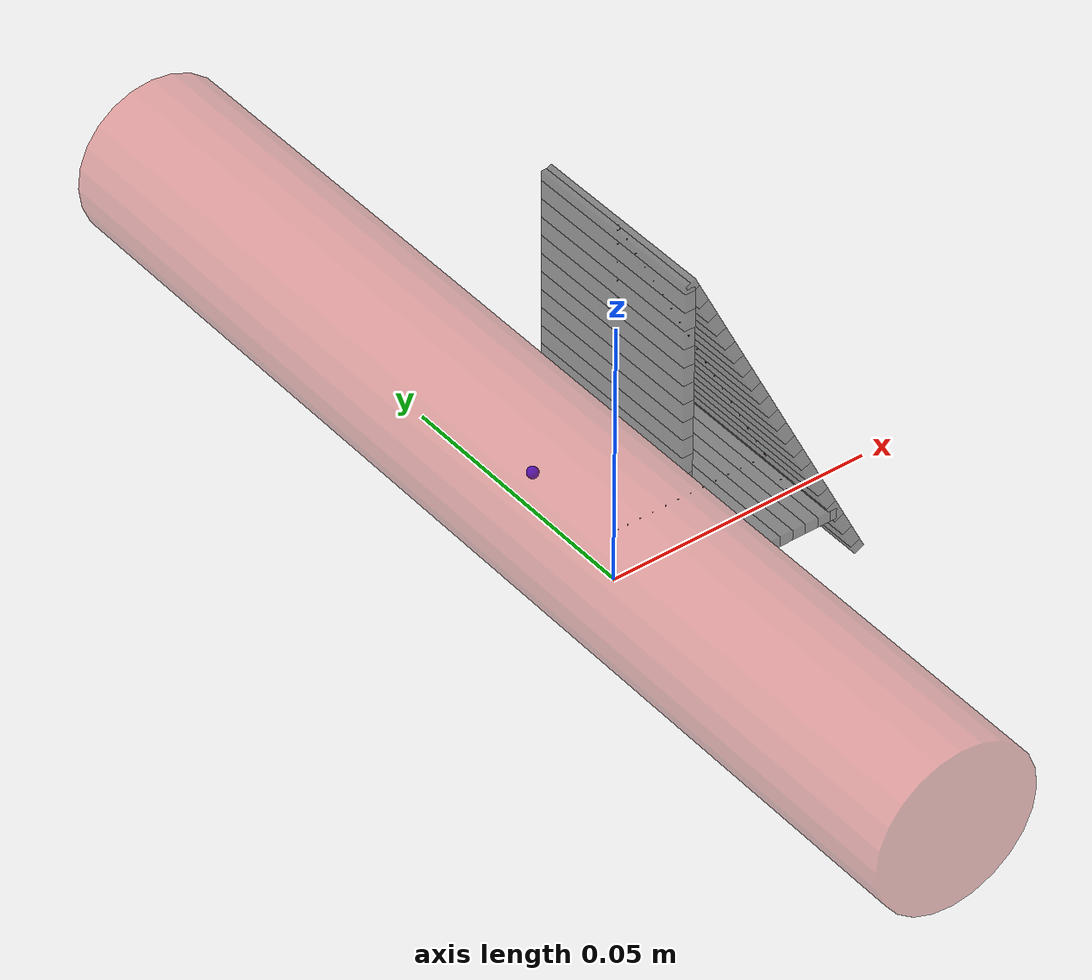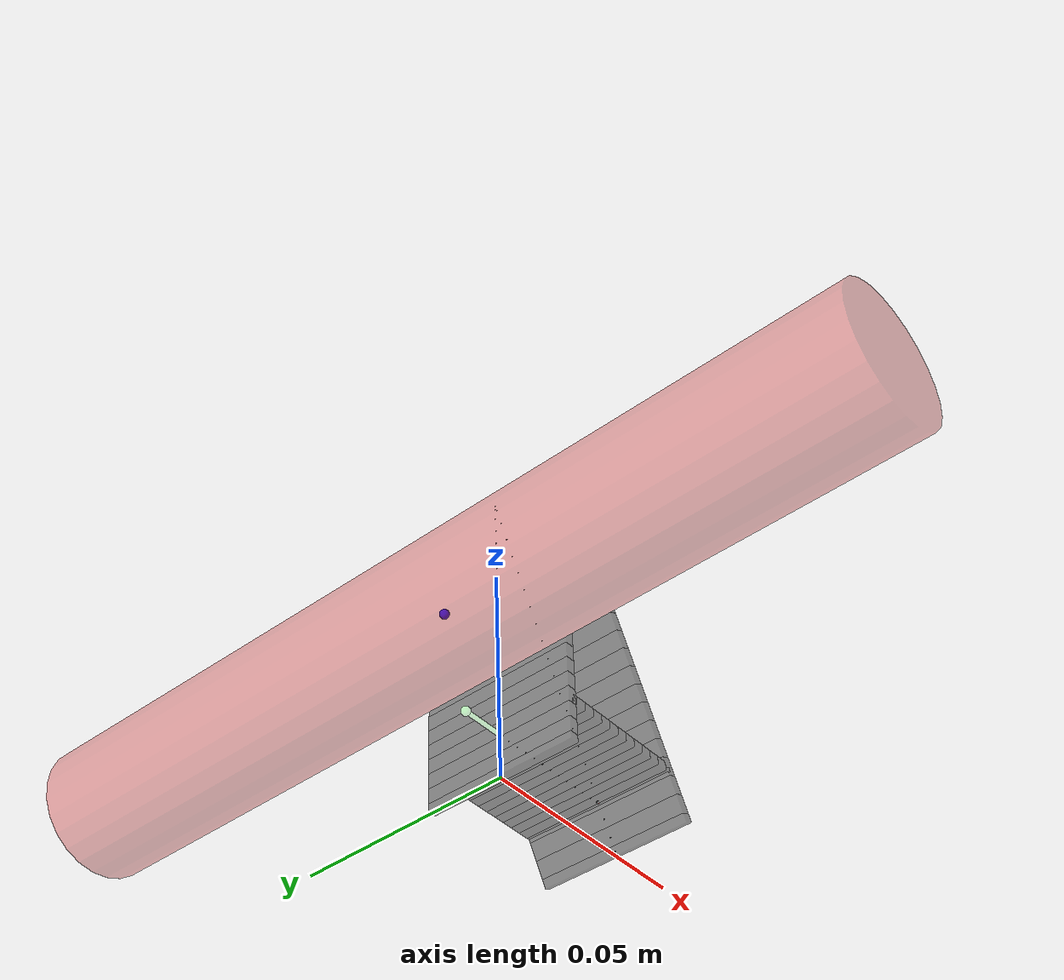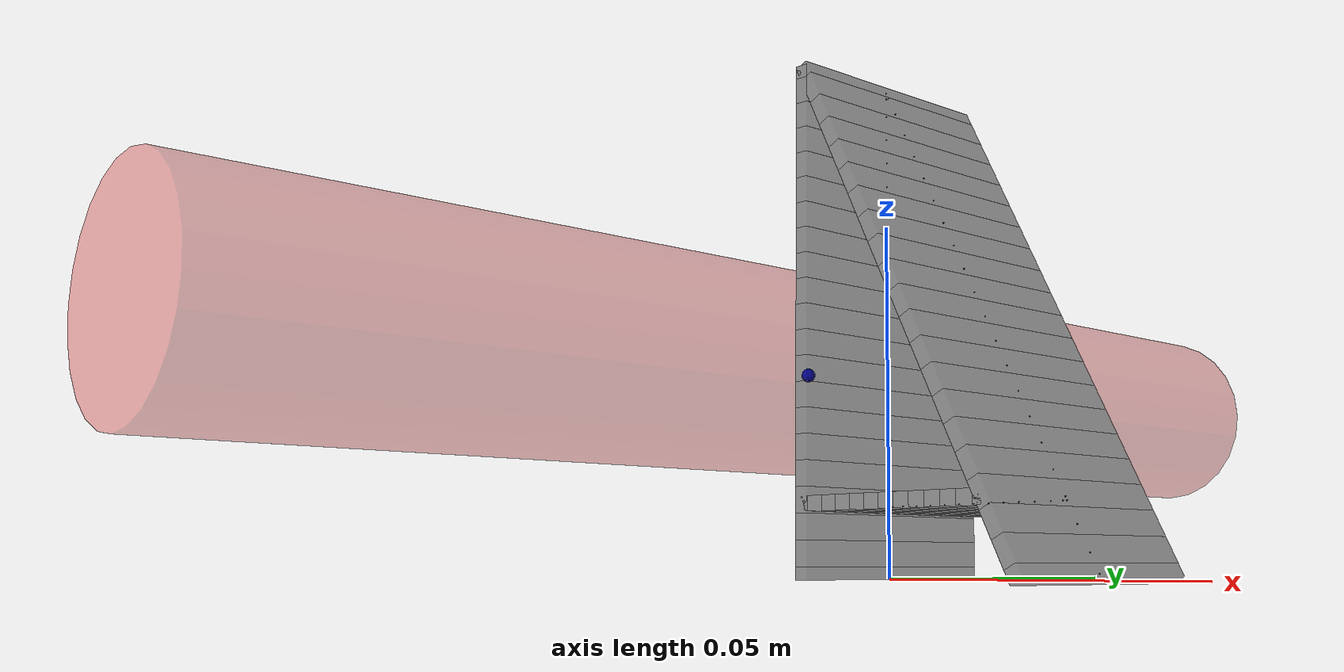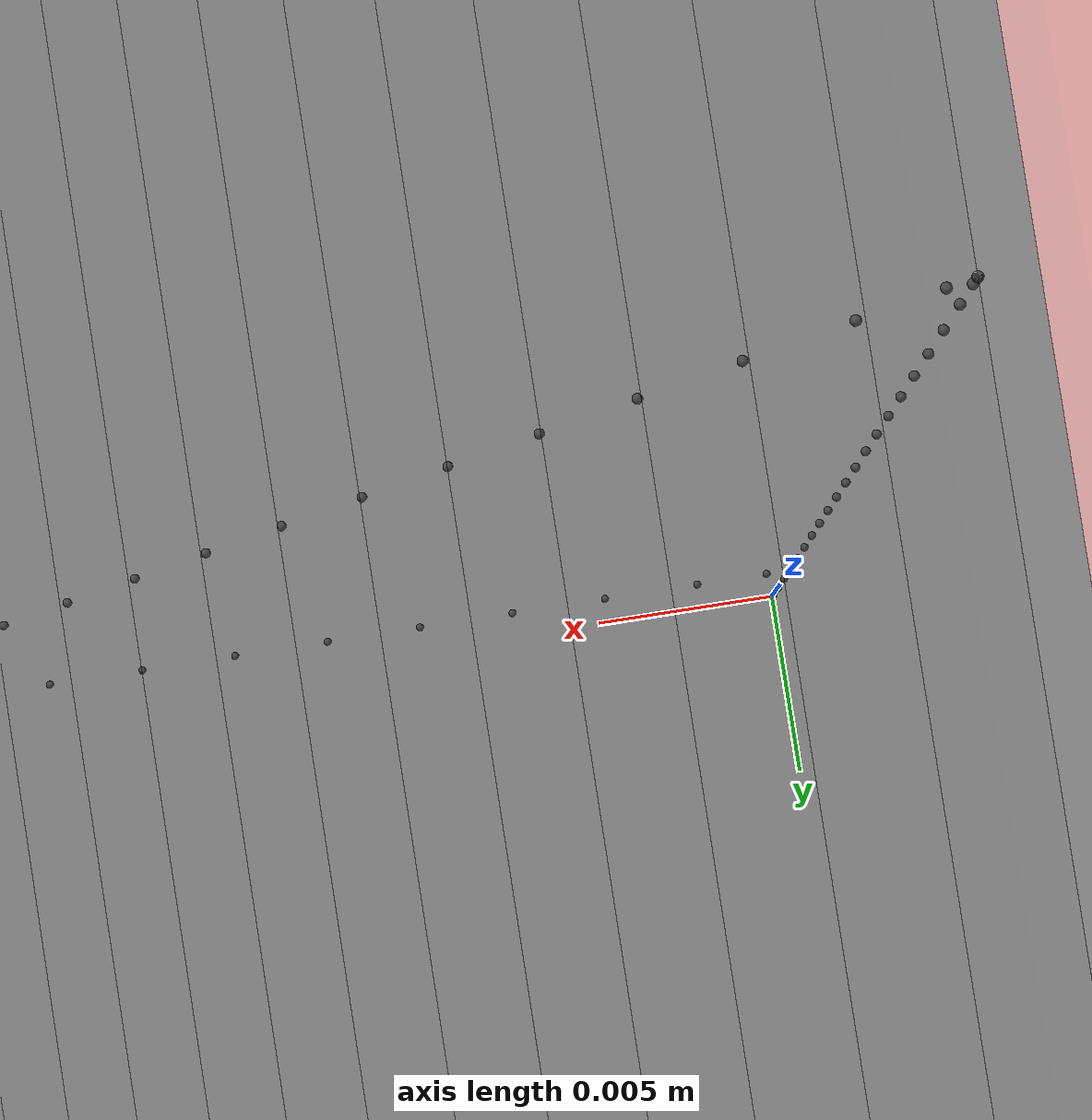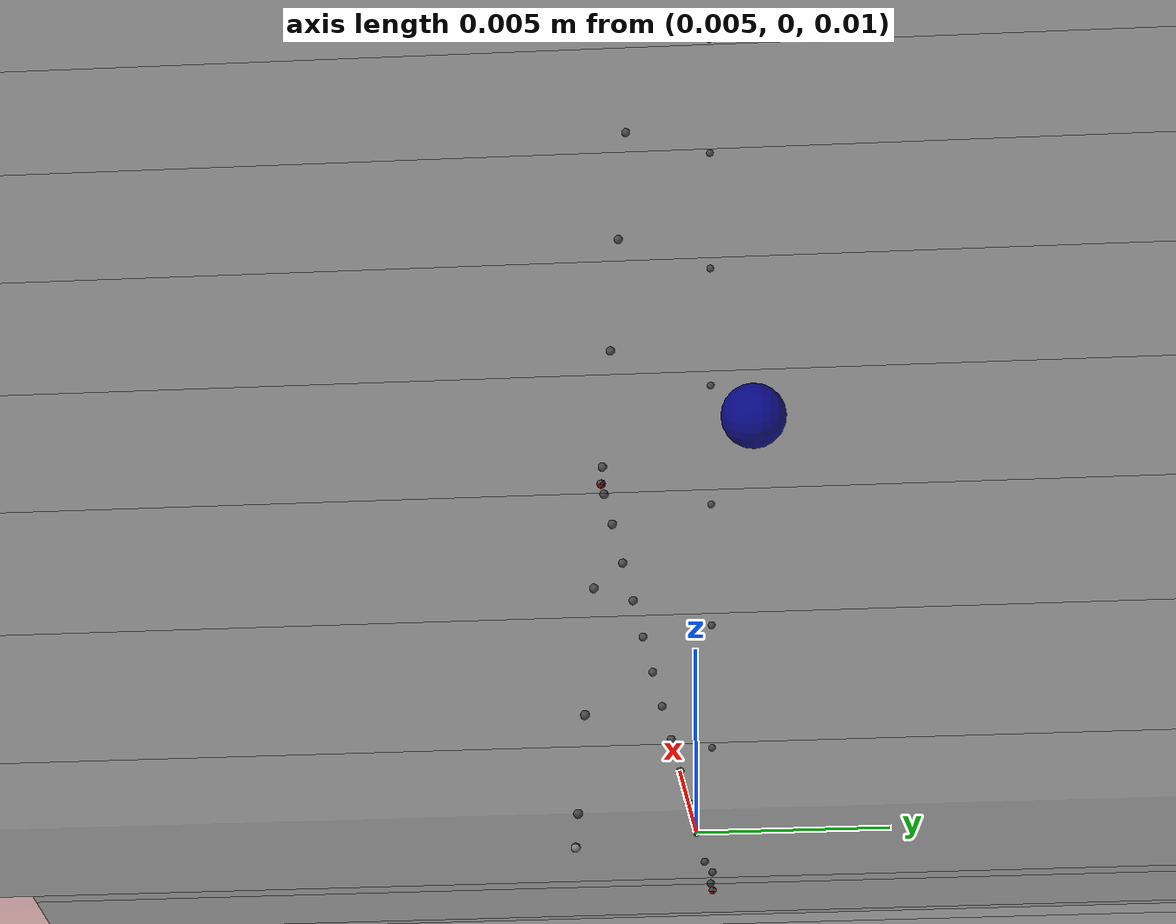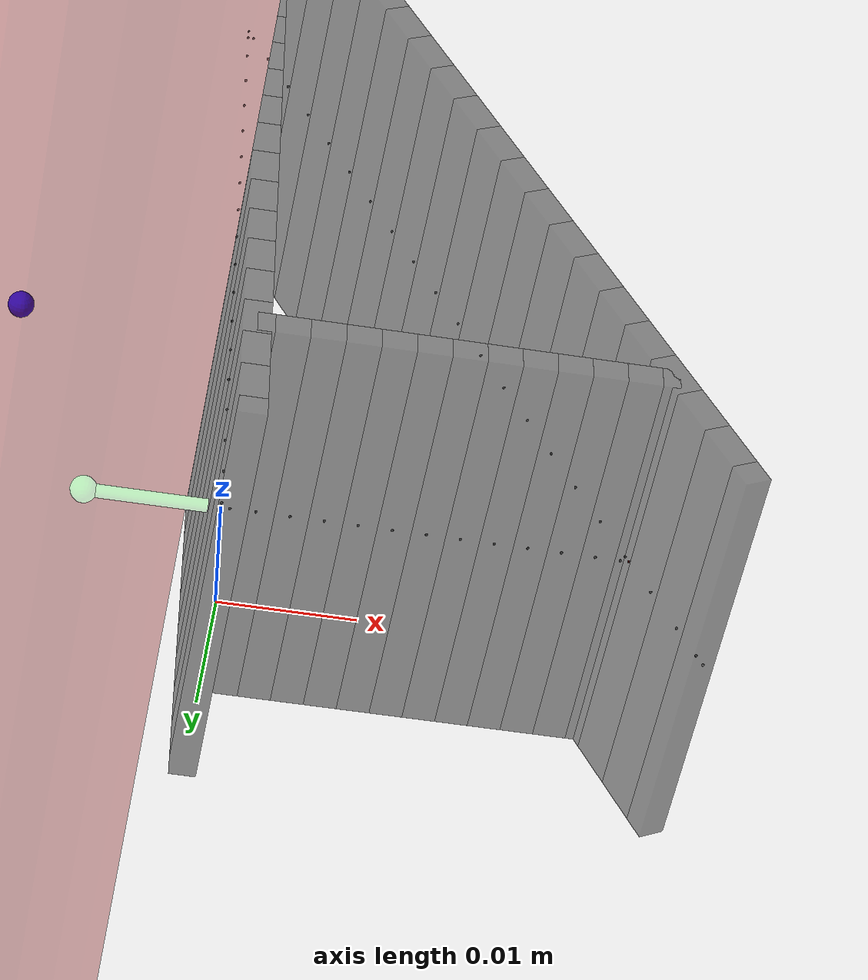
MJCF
<?xml version='1.0' encoding='UTF-8'?>
<mujoco>
    <option timestep="1e-5"/>
    <option gravity="0 0 0"/>
    <option integrator="implicitfast"/>
    <!--Euler, RK4, implicit, implicitfast-->

    <asset>
        <texture type="skybox" builtin="gradient" rgb1="1 1 1" rgb2="1 1 1" width="265" height="256"/>
        <texture name="grid" type="2d" builtin="checker" rgb1="0.1 0.2 0.3" rgb2="0.2 0.3 0.4" width="300" height="300"/>
        <material name="grid" texture="grid" texrepeat="10 10" reflectance="0.2"/>
    </asset>

    <default class="main">
        <geom condim="1" contype="1" conaffinity="0" solref="0.0001 12"/>
        <equality solref="0.0001 12"/>
    </default>

    <worldbody>

    <light pos="0 0 100"/>
    <camera name="side view" pos="0 -0.3 0.025" euler="90 0 0" orthographic="true" fovy="0.1"/>

    <body name="IDF_b_0" pos="0 0 0" euler="0 0 0">
<site name="IDF_b_0_sroot" size="0.0001" pos="0 0 0"/>
<geom name="IDF_b_0_g" type="box" size="0.001 0.0175 0.0008750000000000001" pos="0 0 0.0008750000000000001" rgba="0.1 0.1 0.1 0.5"/>
<site name="IDF_b_0_s" size="0.0001" pos="0 0 0.0008750000000000001"/>
<body name="IDF_b_1" pos="0 0 0.0017500000000000003" euler="0 0 0">
<joint name="IDF_b_1_j" type="hinge" axis="0 1 0" pos="0 0 0" stiffness="0.12333333333333335" damping="0.0006166666666666667"/>
<geom name="IDF_b_1_g" type="box" size="0.001 0.0175 0.0017500000000000003" pos="0 0 0.0017500000000000003" rgba="0.1 0.1 0.1 0.5"/>
<site name="IDF_b_1_s" size="0.0001" pos="0 0 0.0017500000000000003"/>
<body name="IDF_b_2" pos="0 0 0.0035000000000000005" euler="0 0 0">
<joint name="IDF_b_2_j" type="hinge" axis="0 1 0" pos="0 0 0" stiffness="0.12333333333333335" damping="0.0006166666666666667"/>
<geom name="IDF_b_2_g" type="box" size="0.001 0.0175 0.0017500000000000003" pos="0 0 0.0017500000000000003" rgba="0.1 0.1 0.1 0.5"/>
<site name="IDF_b_2_s" size="0.0001" pos="0 0 0.0017500000000000003"/>
<body name="IDF_b_3" pos="0 0 0.0035000000000000005" euler="0 0 0">
<joint name="IDF_b_3_j" type="hinge" axis="0 1 0" pos="0 0 0" stiffness="0.12333333333333335" damping="0.0006166666666666667"/>
<geom name="IDF_b_3_g" type="box" size="0.001 0.0175 0.0017500000000000003" pos="0 0 0.0017500000000000003" rgba="0.1 0.1 0.1 0.5"/>
<site name="IDF_b_3_s" size="0.0001" pos="0 0 0.0017500000000000003"/>
<body name="IDF_b_4" pos="0 0 0.0035000000000000005" euler="0 0 0">
<joint name="IDF_b_4_j" type="hinge" axis="0 1 0" pos="0 0 0" stiffness="0.12333333333333335" damping="0.0006166666666666667"/>
<geom name="IDF_b_4_g" type="box" size="0.001 0.0175 0.0017500000000000003" pos="0 0 0.0017500000000000003" rgba="0.1 0.1 0.1 0.5"/>
<site name="IDF_b_4_s" size="0.0001" pos="0 0 0.0017500000000000003"/>
<body name="IDF_b_5" pos="0 0 0.0035000000000000005" euler="0 0 0">
<joint name="IDF_b_5_j" type="hinge" axis="0 1 0" pos="0 0 0" stiffness="0.12333333333333335" damping="0.0006166666666666667"/>
<geom name="IDF_b_5_g" type="box" size="0.001 0.0175 0.0017500000000000003" pos="0 0 0.0017500000000000003" rgba="0.1 0.1 0.1 0.5"/>
<site name="IDF_b_5_s" size="0.0001" pos="0 0 0.0017500000000000003"/>
<body name="IDF_b_6" pos="0 0 0.0035000000000000005" euler="0 0 0">
<joint name="IDF_b_6_j" type="hinge" axis="0 1 0" pos="0 0 0" stiffness="0.12333333333333335" damping="0.0006166666666666667"/>
<geom name="IDF_b_6_g" type="box" size="0.001 0.0175 0.0017500000000000003" pos="0 0 0.0017500000000000003" rgba="0.1 0.1 0.1 0.5"/>
<site name="IDF_b_6_s" size="0.0001" pos="0 0 0.0017500000000000003"/>
<body name="IDF_b_7" pos="0 0 0.0035000000000000005" euler="0 0 0">
<joint name="IDF_b_7_j" type="hinge" axis="0 1 0" pos="0 0 0" stiffness="0.12333333333333335" damping="0.0006166666666666667"/>
<geom name="IDF_b_7_g" type="box" size="0.001 0.0175 0.0017500000000000003" pos="0 0 0.0017500000000000003" rgba="0.1 0.1 0.1 0.5"/>
<site name="IDF_b_7_s" size="0.0001" pos="0 0 0.0017500000000000003"/>
<body name="IDF_b_8" pos="0 0 0.0035000000000000005" euler="0 0 0">
<joint name="IDF_b_8_j" type="hinge" axis="0 1 0" pos="0 0 0" stiffness="0.12333333333333335" damping="0.0006166666666666667"/>
<geom name="IDF_b_8_g" type="box" size="0.001 0.0175 0.0017500000000000003" pos="0 0 0.0017500000000000003" rgba="0.1 0.1 0.1 0.5"/>
<site name="IDF_b_8_s" size="0.0001" pos="0 0 0.0017500000000000003"/>
<body name="IDF_b_9" pos="0 0 0.0035000000000000005" euler="0 0 0">
<joint name="IDF_b_9_j" type="hinge" axis="0 1 0" pos="0 0 0" stiffness="0.12333333333333335" damping="0.0006166666666666667"/>
<geom name="IDF_b_9_g" type="box" size="0.001 0.0175 0.0017500000000000003" pos="0 0 0.0017500000000000003" rgba="0.1 0.1 0.1 0.5"/>
<site name="IDF_b_9_s" size="0.0001" pos="0 0 0.0017500000000000003"/>
<body name="IDF_b_10" pos="0 0 0.0035000000000000005" euler="0 0 0">
<joint name="IDF_b_10_j" type="hinge" axis="0 1 0" pos="0 0 0" stiffness="0.12333333333333335" damping="0.0006166666666666667"/>
<geom name="IDF_b_10_g" type="box" size="0.001 0.0175 0.0017500000000000003" pos="0 0 0.0017500000000000003" rgba="0.1 0.1 0.1 0.5"/>
<site name="IDF_b_10_s" size="0.0001" pos="0 0 0.0017500000000000003"/>
<body name="IDF_b_11" pos="0 0 0.0035000000000000005" euler="0 0 0">
<joint name="IDF_b_11_j" type="hinge" axis="0 1 0" pos="0 0 0" stiffness="0.12333333333333335" damping="0.0006166666666666667"/>
<geom name="IDF_b_11_g" type="box" size="0.001 0.0175 0.0017500000000000003" pos="0 0 0.0017500000000000003" rgba="0.1 0.1 0.1 0.5"/>
<site name="IDF_b_11_s" size="0.0001" pos="0 0 0.0017500000000000003"/>
<body name="IDF_b_12" pos="0 0 0.0035000000000000005" euler="0 0 0">
<joint name="IDF_b_12_j" type="hinge" axis="0 1 0" pos="0 0 0" stiffness="0.12333333333333335" damping="0.0006166666666666667"/>
<geom name="IDF_b_12_g" type="box" size="0.001 0.0175 0.0017500000000000003" pos="0 0 0.0017500000000000003" rgba="0.1 0.1 0.1 0.5"/>
<site name="IDF_b_12_s" size="0.0001" pos="0 0 0.0017500000000000003"/>
<body name="IDF_b_13" pos="0 0 0.0035000000000000005" euler="0 0 0">
<joint name="IDF_b_13_j" type="hinge" axis="0 1 0" pos="0 0 0" stiffness="0.12333333333333335" damping="0.0006166666666666667"/>
<geom name="IDF_b_13_g" type="box" size="0.001 0.0175 0.0017500000000000003" pos="0 0 0.0017500000000000003" rgba="0.1 0.1 0.1 0.5"/>
<site name="IDF_b_13_s" size="0.0001" pos="0 0 0.0017500000000000003"/>
<body name="IDF_b_14" pos="0 0 0.0035000000000000005" euler="0 0 0">
<joint name="IDF_b_14_j" type="hinge" axis="0 1 0" pos="0 0 0" stiffness="0.12333333333333335" damping="0.0006166666666666667"/>
<geom name="IDF_b_14_g" type="box" size="0.001 0.0175 0.0017500000000000003" pos="0 0 0.0017500000000000003" rgba="0.1 0.1 0.1 0.5"/>
<site name="IDF_b_14_s" size="0.0001" pos="0 0 0.0017500000000000003"/>
<body name="IDF_b_15" pos="0 0 0.0035000000000000005" euler="0 0 0">
<joint name="IDF_b_15_j" type="hinge" axis="0 1 0" pos="0 0 0" stiffness="0.12333333333333335" damping="0.0006166666666666667"/>
<geom name="IDF_b_15_g" type="box" size="0.001 0.0175 0.0017500000000000003" pos="0 0 0.0017500000000000003" rgba="0.1 0.1 0.1 0.5"/>
<site name="IDF_b_15_s" size="0.0001" pos="0 0 0.0017500000000000003"/>
<body name="IDF_b_16" pos="0 0 0.0035000000000000005" euler="0 0 0">
<joint name="IDF_b_16_j" type="hinge" axis="0 1 0" pos="0 0 0" stiffness="0.12333333333333335" damping="0.0006166666666666667"/>
<geom name="IDF_b_16_g" type="box" size="0.001 0.0175 0.0017500000000000003" pos="0 0 0.0017500000000000003" rgba="0.1 0.1 0.1 0.5"/>
<site name="IDF_b_16_s" size="0.0001" pos="0 0 0.0017500000000000003"/>
<body name="IDF_b_17" pos="0 0 0.0035000000000000005" euler="0 0 0">
<joint name="IDF_b_17_j" type="hinge" axis="0 1 0" pos="0 0 0" stiffness="0.12333333333333335" damping="0.0006166666666666667"/>
<geom name="IDF_b_17_g" type="box" size="0.001 0.0175 0.0017500000000000003" pos="0 0 0.0017500000000000003" rgba="0.1 0.1 0.1 0.5"/>
<site name="IDF_b_17_s" size="0.0001" pos="0 0 0.0017500000000000003"/>
<body name="IDF_b_18" pos="0 0 0.0035000000000000005" euler="0 0 0">
<joint name="IDF_b_18_j" type="hinge" axis="0 1 0" pos="0 0 0" stiffness="0.12333333333333335" damping="0.0006166666666666667"/>
<geom name="IDF_b_18_g" type="box" size="0.001 0.0175 0.0017500000000000003" pos="0 0 0.0017500000000000003" rgba="0.1 0.1 0.1 0.5"/>
<site name="IDF_b_18_s" size="0.0001" pos="0 0 0.0017500000000000003"/>
<body name="IDF_b_19" pos="0 0 0.0035000000000000005" euler="0 0 0">
<joint name="IDF_b_19_j" type="hinge" axis="0 1 0" pos="0 0 0" stiffness="0.12333333333333335" damping="0.0006166666666666667"/>
<geom name="IDF_b_19_g" type="box" size="0.001 0.0175 0.0017500000000000003" pos="0 0 0.0017500000000000003" rgba="0.1 0.1 0.1 0.5"/>
<site name="IDF_b_19_s" size="0.0001" pos="0 0 0.0017500000000000003"/>
<body name="IDF_b_20" pos="0 0 0.0035000000000000005" euler="0 0 0">
<joint name="IDF_b_20_j" type="hinge" axis="0 1 0" pos="0 0 0" stiffness="0.12333333333333335" damping="0.0006166666666666667"/>
<geom name="IDF_b_20_g" type="box" size="0.001 0.0175 0.0008750000000000001" pos="0 0 0.0008750000000000001" rgba="0.1 0.1 0.1 0.5"/>
<site name="IDF_b_20_s" size="0.0001" pos="0 0 0.0008750000000000001"/>
<site name="IDF_b_21_s" size="0.0001" pos="0 0 0.0017500000000000003"/>
</body>
</body>
</body>
</body>
</body>
</body>
</body>
</body>
</body>
</body>
</body>
</body>
</body>
</body>
</body>
</body>
</body>
<site name="IDF_b_3_conn_0" size="0.0001" pos="0 0 0.0012499999999999994" rgba="1 0 0 1"/><site name="IDF_b_3_conn_1" size="0.0001" pos="0 0 0.0012499999999999994" rgba="1 0 0 1"/><site name="IDF_b_3_conn_2" size="0.0001" pos="0 0 0.0012499999999999994" rgba="1 0 0 1"/><site name="IDF_b_3_conn_3" size="0.0001" pos="0 0 0.0012499999999999994" rgba="1 0 0 1"/><site name="IDF_b_3_conn_4" size="0.0001" pos="0 0 0.0012499999999999994" rgba="1 0 0 1"/></body>
</body>
</body>
</body><body name="IDB_b_0" pos="0.035 0 0" euler="0 -26.565051177077994 0">
<site name="IDB_b_0_sroot" size="0.0001" pos="0 0 0"/>
<geom name="IDB_b_0_g" type="box" size="0.001000007450580597 0.0175 0.000978279740156158" pos="0 0 0.000978279740156158" rgba="0.1 0.1 0.1 0.5"/>
<site name="IDB_b_0_s" size="0.0001" pos="0 0 0.000978279740156158"/>
<body name="IDB_b_1" pos="0 0 0.001956559480312316" euler="0 0 0">
<joint name="IDB_b_1_j" type="hinge" axis="0 1 0" pos="0 0 0" stiffness="0.11031515258905404" damping="0.0005515757629452702"/>
<geom name="IDB_b_1_g" type="box" size="0.001000007450580597 0.0175 0.001956559480312316" pos="0 0 0.001956559480312316" rgba="0.1 0.1 0.1 0.5"/>
<site name="IDB_b_1_s" size="0.0001" pos="0 0 0.001956559480312316"/>
<body name="IDB_b_2" pos="0 0 0.003913118960624632" euler="0 0 0">
<joint name="IDB_b_2_j" type="hinge" axis="0 1 0" pos="0 0 0" stiffness="0.11031515258905404" damping="0.0005515757629452702"/>
<geom name="IDB_b_2_g" type="box" size="0.001000007450580597 0.0175 0.001956559480312316" pos="0 0 0.001956559480312316" rgba="0.1 0.1 0.1 0.5"/>
<site name="IDB_b_2_s" size="0.0001" pos="0 0 0.001956559480312316"/>
<body name="IDB_b_3" pos="0 0 0.003913118960624632" euler="0 0 0">
<joint name="IDB_b_3_j" type="hinge" axis="0 1 0" pos="0 0 0" stiffness="0.11031515258905404" damping="0.0005515757629452702"/>
<geom name="IDB_b_3_g" type="box" size="0.001000007450580597 0.0175 0.001956559480312316" pos="0 0 0.001956559480312316" rgba="0.1 0.1 0.1 0.5"/>
<site name="IDB_b_3_s" size="0.0001" pos="0 0 0.001956559480312316"/>
<body name="IDB_b_4" pos="0 0 0.003913118960624632" euler="0 0 0">
<joint name="IDB_b_4_j" type="hinge" axis="0 1 0" pos="0 0 0" stiffness="0.11031515258905404" damping="0.0005515757629452702"/>
<geom name="IDB_b_4_g" type="box" size="0.001000007450580597 0.0175 0.001956559480312316" pos="0 0 0.001956559480312316" rgba="0.1 0.1 0.1 0.5"/>
<site name="IDB_b_4_s" size="0.0001" pos="0 0 0.001956559480312316"/>
<body name="IDB_b_5" pos="0 0 0.003913118960624632" euler="0 0 0">
<joint name="IDB_b_5_j" type="hinge" axis="0 1 0" pos="0 0 0" stiffness="0.11031515258905404" damping="0.0005515757629452702"/>
<geom name="IDB_b_5_g" type="box" size="0.001000007450580597 0.0175 0.001956559480312316" pos="0 0 0.001956559480312316" rgba="0.1 0.1 0.1 0.5"/>
<site name="IDB_b_5_s" size="0.0001" pos="0 0 0.001956559480312316"/>
<body name="IDB_b_6" pos="0 0 0.003913118960624632" euler="0 0 0">
<joint name="IDB_b_6_j" type="hinge" axis="0 1 0" pos="0 0 0" stiffness="0.11031515258905404" damping="0.0005515757629452702"/>
<geom name="IDB_b_6_g" type="box" size="0.001000007450580597 0.0175 0.001956559480312316" pos="0 0 0.001956559480312316" rgba="0.1 0.1 0.1 0.5"/>
<site name="IDB_b_6_s" size="0.0001" pos="0 0 0.001956559480312316"/>
<body name="IDB_b_7" pos="0 0 0.003913118960624632" euler="0 0 0">
<joint name="IDB_b_7_j" type="hinge" axis="0 1 0" pos="0 0 0" stiffness="0.11031515258905404" damping="0.0005515757629452702"/>
<geom name="IDB_b_7_g" type="box" size="0.001000007450580597 0.0175 0.001956559480312316" pos="0 0 0.001956559480312316" rgba="0.1 0.1 0.1 0.5"/>
<site name="IDB_b_7_s" size="0.0001" pos="0 0 0.001956559480312316"/>
<body name="IDB_b_8" pos="0 0 0.003913118960624632" euler="0 0 0">
<joint name="IDB_b_8_j" type="hinge" axis="0 1 0" pos="0 0 0" stiffness="0.11031515258905404" damping="0.0005515757629452702"/>
<geom name="IDB_b_8_g" type="box" size="0.001000007450580597 0.0175 0.001956559480312316" pos="0 0 0.001956559480312316" rgba="0.1 0.1 0.1 0.5"/>
<site name="IDB_b_8_s" size="0.0001" pos="0 0 0.001956559480312316"/>
<body name="IDB_b_9" pos="0 0 0.003913118960624632" euler="0 0 0">
<joint name="IDB_b_9_j" type="hinge" axis="0 1 0" pos="0 0 0" stiffness="0.11031515258905404" damping="0.0005515757629452702"/>
<geom name="IDB_b_9_g" type="box" size="0.001000007450580597 0.0175 0.001956559480312316" pos="0 0 0.001956559480312316" rgba="0.1 0.1 0.1 0.5"/>
<site name="IDB_b_9_s" size="0.0001" pos="0 0 0.001956559480312316"/>
<body name="IDB_b_10" pos="0 0 0.003913118960624632" euler="0 0 0">
<joint name="IDB_b_10_j" type="hinge" axis="0 1 0" pos="0 0 0" stiffness="0.11031515258905404" damping="0.0005515757629452702"/>
<geom name="IDB_b_10_g" type="box" size="0.001000007450580597 0.0175 0.001956559480312316" pos="0 0 0.001956559480312316" rgba="0.1 0.1 0.1 0.5"/>
<site name="IDB_b_10_s" size="0.0001" pos="0 0 0.001956559480312316"/>
<body name="IDB_b_11" pos="0 0 0.003913118960624632" euler="0 0 0">
<joint name="IDB_b_11_j" type="hinge" axis="0 1 0" pos="0 0 0" stiffness="0.11031515258905404" damping="0.0005515757629452702"/>
<geom name="IDB_b_11_g" type="box" size="0.001000007450580597 0.0175 0.001956559480312316" pos="0 0 0.001956559480312316" rgba="0.1 0.1 0.1 0.5"/>
<site name="IDB_b_11_s" size="0.0001" pos="0 0 0.001956559480312316"/>
<body name="IDB_b_12" pos="0 0 0.003913118960624632" euler="0 0 0">
<joint name="IDB_b_12_j" type="hinge" axis="0 1 0" pos="0 0 0" stiffness="0.11031515258905404" damping="0.0005515757629452702"/>
<geom name="IDB_b_12_g" type="box" size="0.001000007450580597 0.0175 0.001956559480312316" pos="0 0 0.001956559480312316" rgba="0.1 0.1 0.1 0.5"/>
<site name="IDB_b_12_s" size="0.0001" pos="0 0 0.001956559480312316"/>
<body name="IDB_b_13" pos="0 0 0.003913118960624632" euler="0 0 0">
<joint name="IDB_b_13_j" type="hinge" axis="0 1 0" pos="0 0 0" stiffness="0.11031515258905404" damping="0.0005515757629452702"/>
<geom name="IDB_b_13_g" type="box" size="0.001000007450580597 0.0175 0.001956559480312316" pos="0 0 0.001956559480312316" rgba="0.1 0.1 0.1 0.5"/>
<site name="IDB_b_13_s" size="0.0001" pos="0 0 0.001956559480312316"/>
<body name="IDB_b_14" pos="0 0 0.003913118960624632" euler="0 0 0">
<joint name="IDB_b_14_j" type="hinge" axis="0 1 0" pos="0 0 0" stiffness="0.11031515258905404" damping="0.0005515757629452702"/>
<geom name="IDB_b_14_g" type="box" size="0.001000007450580597 0.0175 0.001956559480312316" pos="0 0 0.001956559480312316" rgba="0.1 0.1 0.1 0.5"/>
<site name="IDB_b_14_s" size="0.0001" pos="0 0 0.001956559480312316"/>
<body name="IDB_b_15" pos="0 0 0.003913118960624632" euler="0 0 0">
<joint name="IDB_b_15_j" type="hinge" axis="0 1 0" pos="0 0 0" stiffness="0.11031515258905404" damping="0.0005515757629452702"/>
<geom name="IDB_b_15_g" type="box" size="0.001000007450580597 0.0175 0.001956559480312316" pos="0 0 0.001956559480312316" rgba="0.1 0.1 0.1 0.5"/>
<site name="IDB_b_15_s" size="0.0001" pos="0 0 0.001956559480312316"/>
<body name="IDB_b_16" pos="0 0 0.003913118960624632" euler="0 0 0">
<joint name="IDB_b_16_j" type="hinge" axis="0 1 0" pos="0 0 0" stiffness="0.11031515258905404" damping="0.0005515757629452702"/>
<geom name="IDB_b_16_g" type="box" size="0.001000007450580597 0.0175 0.001956559480312316" pos="0 0 0.001956559480312316" rgba="0.1 0.1 0.1 0.5"/>
<site name="IDB_b_16_s" size="0.0001" pos="0 0 0.001956559480312316"/>
<body name="IDB_b_17" pos="0 0 0.003913118960624632" euler="0 0 0">
<joint name="IDB_b_17_j" type="hinge" axis="0 1 0" pos="0 0 0" stiffness="0.11031515258905404" damping="0.0005515757629452702"/>
<geom name="IDB_b_17_g" type="box" size="0.001000007450580597 0.0175 0.001956559480312316" pos="0 0 0.001956559480312316" rgba="0.1 0.1 0.1 0.5"/>
<site name="IDB_b_17_s" size="0.0001" pos="0 0 0.001956559480312316"/>
<body name="IDB_b_18" pos="0 0 0.003913118960624632" euler="0 0 0">
<joint name="IDB_b_18_j" type="hinge" axis="0 1 0" pos="0 0 0" stiffness="0.11031515258905404" damping="0.0005515757629452702"/>
<geom name="IDB_b_18_g" type="box" size="0.001000007450580597 0.0175 0.001956559480312316" pos="0 0 0.001956559480312316" rgba="0.1 0.1 0.1 0.5"/>
<site name="IDB_b_18_s" size="0.0001" pos="0 0 0.001956559480312316"/>
<body name="IDB_b_19" pos="0 0 0.003913118960624632" euler="0 0 0">
<joint name="IDB_b_19_j" type="hinge" axis="0 1 0" pos="0 0 0" stiffness="0.11031515258905404" damping="0.0005515757629452702"/>
<geom name="IDB_b_19_g" type="box" size="0.001000007450580597 0.0175 0.001956559480312316" pos="0 0 0.001956559480312316" rgba="0.1 0.1 0.1 0.5"/>
<site name="IDB_b_19_s" size="0.0001" pos="0 0 0.001956559480312316"/>
<body name="IDB_b_20" pos="0 0 0.003913118960624632" euler="0 0 0">
<joint name="IDB_b_20_j" type="hinge" axis="0 1 0" pos="0 0 0" stiffness="0.11031515258905404" damping="0.0005515757629452702"/>
<geom name="IDB_b_20_g" type="box" size="0.001000007450580597 0.0175 0.000978279740156158" pos="0 0 0.000978279740156158" rgba="0.1 0.1 0.1 0.5"/>
<site name="IDB_b_20_s" size="0.0001" pos="0 0 0.000978279740156158"/>
<site name="IDB_b_21_s" size="0.0001" pos="0 0 0.001956559480312316"/>
</body>
</body>
</body>
</body>
</body>
</body>
</body>
</body>
</body>
</body>
</body>
</body>
</body>
</body>
</body>
</body>
</body>
<site name="IDB_b_3_conn_0" size="0.0001" pos="0 0 0.0013975424859373684" rgba="1 0 0 1"/><site name="IDB_b_3_conn_1" size="0.0001" pos="0 0 0.0013975424859373684" rgba="1 0 0 1"/><site name="IDB_b_3_conn_2" size="0.0001" pos="0 0 0.0013975424859373684" rgba="1 0 0 1"/><site name="IDB_b_3_conn_3" size="0.0001" pos="0 0 0.0013975424859373684" rgba="1 0 0 1"/><site name="IDB_b_3_conn_4" size="0.0001" pos="0 0 0.0013975424859373684" rgba="1 0 0 1"/></body>
</body>
</body>
</body><body>
<joint type="free"/>
<body name="IDR0_b_0" pos="0 0 0.01" euler="0 90.0 0">
<site name="IDR0_b_0_sroot" size="0.0001" pos="0 0 0"/>
<geom name="IDR0_b_0_g" type="box" size="0.001 0.0175 0.000625" pos="0 0 0.000625" rgba="0.1 0.1 0.1 0.5"/>
<site name="IDR0_b_0_s" size="0.0001" pos="0 0 0.000625"/>
<body name="IDR0_b_1" pos="0 0 0.00125" euler="0 0 0">
<joint name="IDR0_b_1_j" type="hinge" axis="0 1 0" pos="0 0 0" stiffness="0.17266666666666672" damping="0.0008633333333333336"/>
<geom name="IDR0_b_1_g" type="box" size="0.001 0.0175 0.00125" pos="0 0 0.00125" rgba="0.1 0.1 0.1 0.5"/>
<site name="IDR0_b_1_s" size="0.0001" pos="0 0 0.00125"/>
<body name="IDR0_b_2" pos="0 0 0.0025" euler="0 0 0">
<joint name="IDR0_b_2_j" type="hinge" axis="0 1 0" pos="0 0 0" stiffness="0.17266666666666672" damping="0.0008633333333333336"/>
<geom name="IDR0_b_2_g" type="box" size="0.001 0.0175 0.00125" pos="0 0 0.00125" rgba="0.1 0.1 0.1 0.5"/>
<site name="IDR0_b_2_s" size="0.0001" pos="0 0 0.00125"/>
<body name="IDR0_b_3" pos="0 0 0.0025" euler="0 0 0">
<joint name="IDR0_b_3_j" type="hinge" axis="0 1 0" pos="0 0 0" stiffness="0.17266666666666672" damping="0.0008633333333333336"/>
<geom name="IDR0_b_3_g" type="box" size="0.001 0.0175 0.00125" pos="0 0 0.00125" rgba="0.1 0.1 0.1 0.5"/>
<site name="IDR0_b_3_s" size="0.0001" pos="0 0 0.00125"/>
<body name="IDR0_b_4" pos="0 0 0.0025" euler="0 0 0">
<joint name="IDR0_b_4_j" type="hinge" axis="0 1 0" pos="0 0 0" stiffness="0.17266666666666672" damping="0.0008633333333333336"/>
<geom name="IDR0_b_4_g" type="box" size="0.001 0.0175 0.00125" pos="0 0 0.00125" rgba="0.1 0.1 0.1 0.5"/>
<site name="IDR0_b_4_s" size="0.0001" pos="0 0 0.00125"/>
<body name="IDR0_b_5" pos="0 0 0.0025" euler="0 0 0">
<joint name="IDR0_b_5_j" type="hinge" axis="0 1 0" pos="0 0 0" stiffness="0.17266666666666672" damping="0.0008633333333333336"/>
<geom name="IDR0_b_5_g" type="box" size="0.001 0.0175 0.00125" pos="0 0 0.00125" rgba="0.1 0.1 0.1 0.5"/>
<site name="IDR0_b_5_s" size="0.0001" pos="0 0 0.00125"/>
<body name="IDR0_b_6" pos="0 0 0.0025" euler="0 0 0">
<joint name="IDR0_b_6_j" type="hinge" axis="0 1 0" pos="0 0 0" stiffness="0.17266666666666672" damping="0.0008633333333333336"/>
<geom name="IDR0_b_6_g" type="box" size="0.001 0.0175 0.00125" pos="0 0 0.00125" rgba="0.1 0.1 0.1 0.5"/>
<site name="IDR0_b_6_s" size="0.0001" pos="0 0 0.00125"/>
<body name="IDR0_b_7" pos="0 0 0.0025" euler="0 0 0">
<joint name="IDR0_b_7_j" type="hinge" axis="0 1 0" pos="0 0 0" stiffness="0.17266666666666672" damping="0.0008633333333333336"/>
<geom name="IDR0_b_7_g" type="box" size="0.001 0.0175 0.00125" pos="0 0 0.00125" rgba="0.1 0.1 0.1 0.5"/>
<site name="IDR0_b_7_s" size="0.0001" pos="0 0 0.00125"/>
<body name="IDR0_b_8" pos="0 0 0.0025" euler="0 0 0">
<joint name="IDR0_b_8_j" type="hinge" axis="0 1 0" pos="0 0 0" stiffness="0.17266666666666672" damping="0.0008633333333333336"/>
<geom name="IDR0_b_8_g" type="box" size="0.001 0.0175 0.00125" pos="0 0 0.00125" rgba="0.1 0.1 0.1 0.5"/>
<site name="IDR0_b_8_s" size="0.0001" pos="0 0 0.00125"/>
<body name="IDR0_b_9" pos="0 0 0.0025" euler="0 0 0">
<joint name="IDR0_b_9_j" type="hinge" axis="0 1 0" pos="0 0 0" stiffness="0.17266666666666672" damping="0.0008633333333333336"/>
<geom name="IDR0_b_9_g" type="box" size="0.001 0.0175 0.00125" pos="0 0 0.00125" rgba="0.1 0.1 0.1 0.5"/>
<site name="IDR0_b_9_s" size="0.0001" pos="0 0 0.00125"/>
<body name="IDR0_b_10" pos="0 0 0.0025" euler="0 0 0">
<joint name="IDR0_b_10_j" type="hinge" axis="0 1 0" pos="0 0 0" stiffness="0.17266666666666672" damping="0.0008633333333333336"/>
<geom name="IDR0_b_10_g" type="box" size="0.001 0.0175 0.00125" pos="0 0 0.00125" rgba="0.1 0.1 0.1 0.5"/>
<site name="IDR0_b_10_s" size="0.0001" pos="0 0 0.00125"/>
<body name="IDR0_b_11" pos="0 0 0.0025" euler="0 0 0">
<joint name="IDR0_b_11_j" type="hinge" axis="0 1 0" pos="0 0 0" stiffness="0.17266666666666672" damping="0.0008633333333333336"/>
<geom name="IDR0_b_11_g" type="box" size="0.001 0.0175 0.00125" pos="0 0 0.00125" rgba="0.1 0.1 0.1 0.5"/>
<site name="IDR0_b_11_s" size="0.0001" pos="0 0 0.00125"/>
<body name="IDR0_b_12" pos="0 0 0.0025" euler="0 0 0">
<joint name="IDR0_b_12_j" type="hinge" axis="0 1 0" pos="0 0 0" stiffness="0.17266666666666672" damping="0.0008633333333333336"/>
<geom name="IDR0_b_12_g" type="box" size="0.001 0.0175 0.000625" pos="0 0 0.000625" rgba="0.1 0.1 0.1 0.5"/>
<site name="IDR0_b_12_s" size="0.0001" pos="0 0 0.000625"/>
<site name="IDR0_b_13_s" size="0.0001" pos="0 0 0.00125"/>
</body>
</body>
</body>
</body>
</body>
</body>
</body>
</body>
</body>
</body>
</body>
</body>
</body>
</body><body>
<joint type="free"/>
<body name="IDR1_b_0" pos="0 0 0.01" euler="0 90.0 0">
<site name="IDR1_b_0_sroot" size="0.0001" pos="0 0 0"/>
<geom name="IDR1_b_0_g" type="box" size="0.001 0.0175 0.000625" pos="0 0 0.000625" rgba="0.1 0.1 0.1 0.5"/>
<site name="IDR1_b_0_s" size="0.0001" pos="0 0 0.000625"/>
<body name="IDR1_b_1" pos="0 0 0.00125" euler="0 0 0">
<joint name="IDR1_b_1_j" type="hinge" axis="0 1 0" pos="0 0 0" stiffness="0.17266666666666672" damping="0.0008633333333333336"/>
<geom name="IDR1_b_1_g" type="box" size="0.001 0.0175 0.00125" pos="0 0 0.00125" rgba="0.1 0.1 0.1 0.5"/>
<site name="IDR1_b_1_s" size="0.0001" pos="0 0 0.00125"/>
<body name="IDR1_b_2" pos="0 0 0.0025" euler="0 0 0">
<joint name="IDR1_b_2_j" type="hinge" axis="0 1 0" pos="0 0 0" stiffness="0.17266666666666672" damping="0.0008633333333333336"/>
<geom name="IDR1_b_2_g" type="box" size="0.001 0.0175 0.00125" pos="0 0 0.00125" rgba="0.1 0.1 0.1 0.5"/>
<site name="IDR1_b_2_s" size="0.0001" pos="0 0 0.00125"/>
<body name="IDR1_b_3" pos="0 0 0.0025" euler="0 0 0">
<joint name="IDR1_b_3_j" type="hinge" axis="0 1 0" pos="0 0 0" stiffness="0.17266666666666672" damping="0.0008633333333333336"/>
<geom name="IDR1_b_3_g" type="box" size="0.001 0.0175 0.00125" pos="0 0 0.00125" rgba="0.1 0.1 0.1 0.5"/>
<site name="IDR1_b_3_s" size="0.0001" pos="0 0 0.00125"/>
<body name="IDR1_b_4" pos="0 0 0.0025" euler="0 0 0">
<joint name="IDR1_b_4_j" type="hinge" axis="0 1 0" pos="0 0 0" stiffness="0.17266666666666672" damping="0.0008633333333333336"/>
<geom name="IDR1_b_4_g" type="box" size="0.001 0.0175 0.00125" pos="0 0 0.00125" rgba="0.1 0.1 0.1 0.5"/>
<site name="IDR1_b_4_s" size="0.0001" pos="0 0 0.00125"/>
<body name="IDR1_b_5" pos="0 0 0.0025" euler="0 0 0">
<joint name="IDR1_b_5_j" type="hinge" axis="0 1 0" pos="0 0 0" stiffness="0.17266666666666672" damping="0.0008633333333333336"/>
<geom name="IDR1_b_5_g" type="box" size="0.001 0.0175 0.00125" pos="0 0 0.00125" rgba="0.1 0.1 0.1 0.5"/>
<site name="IDR1_b_5_s" size="0.0001" pos="0 0 0.00125"/>
<body name="IDR1_b_6" pos="0 0 0.0025" euler="0 0 0">
<joint name="IDR1_b_6_j" type="hinge" axis="0 1 0" pos="0 0 0" stiffness="0.17266666666666672" damping="0.0008633333333333336"/>
<geom name="IDR1_b_6_g" type="box" size="0.001 0.0175 0.00125" pos="0 0 0.00125" rgba="0.1 0.1 0.1 0.5"/>
<site name="IDR1_b_6_s" size="0.0001" pos="0 0 0.00125"/>
<body name="IDR1_b_7" pos="0 0 0.0025" euler="0 0 0">
<joint name="IDR1_b_7_j" type="hinge" axis="0 1 0" pos="0 0 0" stiffness="0.17266666666666672" damping="0.0008633333333333336"/>
<geom name="IDR1_b_7_g" type="box" size="0.001 0.0175 0.00125" pos="0 0 0.00125" rgba="0.1 0.1 0.1 0.5"/>
<site name="IDR1_b_7_s" size="0.0001" pos="0 0 0.00125"/>
<body name="IDR1_b_8" pos="0 0 0.0025" euler="0 0 0">
<joint name="IDR1_b_8_j" type="hinge" axis="0 1 0" pos="0 0 0" stiffness="0.17266666666666672" damping="0.0008633333333333336"/>
<geom name="IDR1_b_8_g" type="box" size="0.001 0.0175 0.00125" pos="0 0 0.00125" rgba="0.1 0.1 0.1 0.5"/>
<site name="IDR1_b_8_s" size="0.0001" pos="0 0 0.00125"/>
<body name="IDR1_b_9" pos="0 0 0.0025" euler="0 0 0">
<joint name="IDR1_b_9_j" type="hinge" axis="0 1 0" pos="0 0 0" stiffness="0.17266666666666672" damping="0.0008633333333333336"/>
<geom name="IDR1_b_9_g" type="box" size="0.001 0.0175 0.00125" pos="0 0 0.00125" rgba="0.1 0.1 0.1 0.5"/>
<site name="IDR1_b_9_s" size="0.0001" pos="0 0 0.00125"/>
<body name="IDR1_b_10" pos="0 0 0.0025" euler="0 0 0">
<joint name="IDR1_b_10_j" type="hinge" axis="0 1 0" pos="0 0 0" stiffness="0.17266666666666672" damping="0.0008633333333333336"/>
<geom name="IDR1_b_10_g" type="box" size="0.001 0.0175 0.00125" pos="0 0 0.00125" rgba="0.1 0.1 0.1 0.5"/>
<site name="IDR1_b_10_s" size="0.0001" pos="0 0 0.00125"/>
<body name="IDR1_b_11" pos="0 0 0.0025" euler="0 0 0">
<joint name="IDR1_b_11_j" type="hinge" axis="0 1 0" pos="0 0 0" stiffness="0.17266666666666672" damping="0.0008633333333333336"/>
<geom name="IDR1_b_11_g" type="box" size="0.001 0.0175 0.00125" pos="0 0 0.00125" rgba="0.1 0.1 0.1 0.5"/>
<site name="IDR1_b_11_s" size="0.0001" pos="0 0 0.00125"/>
<body name="IDR1_b_12" pos="0 0 0.0025" euler="0 0 0">
<joint name="IDR1_b_12_j" type="hinge" axis="0 1 0" pos="0 0 0" stiffness="0.17266666666666672" damping="0.0008633333333333336"/>
<geom name="IDR1_b_12_g" type="box" size="0.001 0.0175 0.000625" pos="0 0 0.000625" rgba="0.1 0.1 0.1 0.5"/>
<site name="IDR1_b_12_s" size="0.0001" pos="0 0 0.000625"/>
<site name="IDR1_b_13_s" size="0.0001" pos="0 0 0.00125"/>
</body>
</body>
</body>
</body>
</body>
</body>
</body>
</body>
</body>
</body>
</body>
</body>
</body>
</body><body>
<joint type="free"/>
<body name="IDR2_b_0" pos="0 0 0.01" euler="0 90.0 0">
<site name="IDR2_b_0_sroot" size="0.0001" pos="0 0 0"/>
<geom name="IDR2_b_0_g" type="box" size="0.001 0.0175 0.000625" pos="0 0 0.000625" rgba="0.1 0.1 0.1 0.5"/>
<site name="IDR2_b_0_s" size="0.0001" pos="0 0 0.000625"/>
<body name="IDR2_b_1" pos="0 0 0.00125" euler="0 0 0">
<joint name="IDR2_b_1_j" type="hinge" axis="0 1 0" pos="0 0 0" stiffness="0.17266666666666672" damping="0.0008633333333333336"/>
<geom name="IDR2_b_1_g" type="box" size="0.001 0.0175 0.00125" pos="0 0 0.00125" rgba="0.1 0.1 0.1 0.5"/>
<site name="IDR2_b_1_s" size="0.0001" pos="0 0 0.00125"/>
<body name="IDR2_b_2" pos="0 0 0.0025" euler="0 0 0">
<joint name="IDR2_b_2_j" type="hinge" axis="0 1 0" pos="0 0 0" stiffness="0.17266666666666672" damping="0.0008633333333333336"/>
<geom name="IDR2_b_2_g" type="box" size="0.001 0.0175 0.00125" pos="0 0 0.00125" rgba="0.1 0.1 0.1 0.5"/>
<site name="IDR2_b_2_s" size="0.0001" pos="0 0 0.00125"/>
<body name="IDR2_b_3" pos="0 0 0.0025" euler="0 0 0">
<joint name="IDR2_b_3_j" type="hinge" axis="0 1 0" pos="0 0 0" stiffness="0.17266666666666672" damping="0.0008633333333333336"/>
<geom name="IDR2_b_3_g" type="box" size="0.001 0.0175 0.00125" pos="0 0 0.00125" rgba="0.1 0.1 0.1 0.5"/>
<site name="IDR2_b_3_s" size="0.0001" pos="0 0 0.00125"/>
<body name="IDR2_b_4" pos="0 0 0.0025" euler="0 0 0">
<joint name="IDR2_b_4_j" type="hinge" axis="0 1 0" pos="0 0 0" stiffness="0.17266666666666672" damping="0.0008633333333333336"/>
<geom name="IDR2_b_4_g" type="box" size="0.001 0.0175 0.00125" pos="0 0 0.00125" rgba="0.1 0.1 0.1 0.5"/>
<site name="IDR2_b_4_s" size="0.0001" pos="0 0 0.00125"/>
<body name="IDR2_b_5" pos="0 0 0.0025" euler="0 0 0">
<joint name="IDR2_b_5_j" type="hinge" axis="0 1 0" pos="0 0 0" stiffness="0.17266666666666672" damping="0.0008633333333333336"/>
<geom name="IDR2_b_5_g" type="box" size="0.001 0.0175 0.00125" pos="0 0 0.00125" rgba="0.1 0.1 0.1 0.5"/>
<site name="IDR2_b_5_s" size="0.0001" pos="0 0 0.00125"/>
<body name="IDR2_b_6" pos="0 0 0.0025" euler="0 0 0">
<joint name="IDR2_b_6_j" type="hinge" axis="0 1 0" pos="0 0 0" stiffness="0.17266666666666672" damping="0.0008633333333333336"/>
<geom name="IDR2_b_6_g" type="box" size="0.001 0.0175 0.00125" pos="0 0 0.00125" rgba="0.1 0.1 0.1 0.5"/>
<site name="IDR2_b_6_s" size="0.0001" pos="0 0 0.00125"/>
<body name="IDR2_b_7" pos="0 0 0.0025" euler="0 0 0">
<joint name="IDR2_b_7_j" type="hinge" axis="0 1 0" pos="0 0 0" stiffness="0.17266666666666672" damping="0.0008633333333333336"/>
<geom name="IDR2_b_7_g" type="box" size="0.001 0.0175 0.00125" pos="0 0 0.00125" rgba="0.1 0.1 0.1 0.5"/>
<site name="IDR2_b_7_s" size="0.0001" pos="0 0 0.00125"/>
<body name="IDR2_b_8" pos="0 0 0.0025" euler="0 0 0">
<joint name="IDR2_b_8_j" type="hinge" axis="0 1 0" pos="0 0 0" stiffness="0.17266666666666672" damping="0.0008633333333333336"/>
<geom name="IDR2_b_8_g" type="box" size="0.001 0.0175 0.00125" pos="0 0 0.00125" rgba="0.1 0.1 0.1 0.5"/>
<site name="IDR2_b_8_s" size="0.0001" pos="0 0 0.00125"/>
<body name="IDR2_b_9" pos="0 0 0.0025" euler="0 0 0">
<joint name="IDR2_b_9_j" type="hinge" axis="0 1 0" pos="0 0 0" stiffness="0.17266666666666672" damping="0.0008633333333333336"/>
<geom name="IDR2_b_9_g" type="box" size="0.001 0.0175 0.00125" pos="0 0 0.00125" rgba="0.1 0.1 0.1 0.5"/>
<site name="IDR2_b_9_s" size="0.0001" pos="0 0 0.00125"/>
<body name="IDR2_b_10" pos="0 0 0.0025" euler="0 0 0">
<joint name="IDR2_b_10_j" type="hinge" axis="0 1 0" pos="0 0 0" stiffness="0.17266666666666672" damping="0.0008633333333333336"/>
<geom name="IDR2_b_10_g" type="box" size="0.001 0.0175 0.00125" pos="0 0 0.00125" rgba="0.1 0.1 0.1 0.5"/>
<site name="IDR2_b_10_s" size="0.0001" pos="0 0 0.00125"/>
<body name="IDR2_b_11" pos="0 0 0.0025" euler="0 0 0">
<joint name="IDR2_b_11_j" type="hinge" axis="0 1 0" pos="0 0 0" stiffness="0.17266666666666672" damping="0.0008633333333333336"/>
<geom name="IDR2_b_11_g" type="box" size="0.001 0.0175 0.00125" pos="0 0 0.00125" rgba="0.1 0.1 0.1 0.5"/>
<site name="IDR2_b_11_s" size="0.0001" pos="0 0 0.00125"/>
<body name="IDR2_b_12" pos="0 0 0.0025" euler="0 0 0">
<joint name="IDR2_b_12_j" type="hinge" axis="0 1 0" pos="0 0 0" stiffness="0.17266666666666672" damping="0.0008633333333333336"/>
<geom name="IDR2_b_12_g" type="box" size="0.001 0.0175 0.000625" pos="0 0 0.000625" rgba="0.1 0.1 0.1 0.5"/>
<site name="IDR2_b_12_s" size="0.0001" pos="0 0 0.000625"/>
<site name="IDR2_b_13_s" size="0.0001" pos="0 0 0.00125"/>
</body>
</body>
</body>
</body>
</body>
</body>
</body>
</body>
</body>
</body>
</body>
</body>
</body>
</body><body>
<joint type="free"/>
<body name="IDR3_b_0" pos="0 0 0.01" euler="0 90.0 0">
<site name="IDR3_b_0_sroot" size="0.0001" pos="0 0 0"/>
<geom name="IDR3_b_0_g" type="box" size="0.001 0.0175 0.000625" pos="0 0 0.000625" rgba="0.1 0.1 0.1 0.5"/>
<site name="IDR3_b_0_s" size="0.0001" pos="0 0 0.000625"/>
<body name="IDR3_b_1" pos="0 0 0.00125" euler="0 0 0">
<joint name="IDR3_b_1_j" type="hinge" axis="0 1 0" pos="0 0 0" stiffness="0.17266666666666672" damping="0.0008633333333333336"/>
<geom name="IDR3_b_1_g" type="box" size="0.001 0.0175 0.00125" pos="0 0 0.00125" rgba="0.1 0.1 0.1 0.5"/>
<site name="IDR3_b_1_s" size="0.0001" pos="0 0 0.00125"/>
<body name="IDR3_b_2" pos="0 0 0.0025" euler="0 0 0">
<joint name="IDR3_b_2_j" type="hinge" axis="0 1 0" pos="0 0 0" stiffness="0.17266666666666672" damping="0.0008633333333333336"/>
<geom name="IDR3_b_2_g" type="box" size="0.001 0.0175 0.00125" pos="0 0 0.00125" rgba="0.1 0.1 0.1 0.5"/>
<site name="IDR3_b_2_s" size="0.0001" pos="0 0 0.00125"/>
<body name="IDR3_b_3" pos="0 0 0.0025" euler="0 0 0">
<joint name="IDR3_b_3_j" type="hinge" axis="0 1 0" pos="0 0 0" stiffness="0.17266666666666672" damping="0.0008633333333333336"/>
<geom name="IDR3_b_3_g" type="box" size="0.001 0.0175 0.00125" pos="0 0 0.00125" rgba="0.1 0.1 0.1 0.5"/>
<site name="IDR3_b_3_s" size="0.0001" pos="0 0 0.00125"/>
<body name="IDR3_b_4" pos="0 0 0.0025" euler="0 0 0">
<joint name="IDR3_b_4_j" type="hinge" axis="0 1 0" pos="0 0 0" stiffness="0.17266666666666672" damping="0.0008633333333333336"/>
<geom name="IDR3_b_4_g" type="box" size="0.001 0.0175 0.00125" pos="0 0 0.00125" rgba="0.1 0.1 0.1 0.5"/>
<site name="IDR3_b_4_s" size="0.0001" pos="0 0 0.00125"/>
<body name="IDR3_b_5" pos="0 0 0.0025" euler="0 0 0">
<joint name="IDR3_b_5_j" type="hinge" axis="0 1 0" pos="0 0 0" stiffness="0.17266666666666672" damping="0.0008633333333333336"/>
<geom name="IDR3_b_5_g" type="box" size="0.001 0.0175 0.00125" pos="0 0 0.00125" rgba="0.1 0.1 0.1 0.5"/>
<site name="IDR3_b_5_s" size="0.0001" pos="0 0 0.00125"/>
<body name="IDR3_b_6" pos="0 0 0.0025" euler="0 0 0">
<joint name="IDR3_b_6_j" type="hinge" axis="0 1 0" pos="0 0 0" stiffness="0.17266666666666672" damping="0.0008633333333333336"/>
<geom name="IDR3_b_6_g" type="box" size="0.001 0.0175 0.00125" pos="0 0 0.00125" rgba="0.1 0.1 0.1 0.5"/>
<site name="IDR3_b_6_s" size="0.0001" pos="0 0 0.00125"/>
<body name="IDR3_b_7" pos="0 0 0.0025" euler="0 0 0">
<joint name="IDR3_b_7_j" type="hinge" axis="0 1 0" pos="0 0 0" stiffness="0.17266666666666672" damping="0.0008633333333333336"/>
<geom name="IDR3_b_7_g" type="box" size="0.001 0.0175 0.00125" pos="0 0 0.00125" rgba="0.1 0.1 0.1 0.5"/>
<site name="IDR3_b_7_s" size="0.0001" pos="0 0 0.00125"/>
<body name="IDR3_b_8" pos="0 0 0.0025" euler="0 0 0">
<joint name="IDR3_b_8_j" type="hinge" axis="0 1 0" pos="0 0 0" stiffness="0.17266666666666672" damping="0.0008633333333333336"/>
<geom name="IDR3_b_8_g" type="box" size="0.001 0.0175 0.00125" pos="0 0 0.00125" rgba="0.1 0.1 0.1 0.5"/>
<site name="IDR3_b_8_s" size="0.0001" pos="0 0 0.00125"/>
<body name="IDR3_b_9" pos="0 0 0.0025" euler="0 0 0">
<joint name="IDR3_b_9_j" type="hinge" axis="0 1 0" pos="0 0 0" stiffness="0.17266666666666672" damping="0.0008633333333333336"/>
<geom name="IDR3_b_9_g" type="box" size="0.001 0.0175 0.00125" pos="0 0 0.00125" rgba="0.1 0.1 0.1 0.5"/>
<site name="IDR3_b_9_s" size="0.0001" pos="0 0 0.00125"/>
<body name="IDR3_b_10" pos="0 0 0.0025" euler="0 0 0">
<joint name="IDR3_b_10_j" type="hinge" axis="0 1 0" pos="0 0 0" stiffness="0.17266666666666672" damping="0.0008633333333333336"/>
<geom name="IDR3_b_10_g" type="box" size="0.001 0.0175 0.00125" pos="0 0 0.00125" rgba="0.1 0.1 0.1 0.5"/>
<site name="IDR3_b_10_s" size="0.0001" pos="0 0 0.00125"/>
<body name="IDR3_b_11" pos="0 0 0.0025" euler="0 0 0">
<joint name="IDR3_b_11_j" type="hinge" axis="0 1 0" pos="0 0 0" stiffness="0.17266666666666672" damping="0.0008633333333333336"/>
<geom name="IDR3_b_11_g" type="box" size="0.001 0.0175 0.00125" pos="0 0 0.00125" rgba="0.1 0.1 0.1 0.5"/>
<site name="IDR3_b_11_s" size="0.0001" pos="0 0 0.00125"/>
<body name="IDR3_b_12" pos="0 0 0.0025" euler="0 0 0">
<joint name="IDR3_b_12_j" type="hinge" axis="0 1 0" pos="0 0 0" stiffness="0.17266666666666672" damping="0.0008633333333333336"/>
<geom name="IDR3_b_12_g" type="box" size="0.001 0.0175 0.000625" pos="0 0 0.000625" rgba="0.1 0.1 0.1 0.5"/>
<site name="IDR3_b_12_s" size="0.0001" pos="0 0 0.000625"/>
<site name="IDR3_b_13_s" size="0.0001" pos="0 0 0.00125"/>
</body>
</body>
</body>
</body>
</body>
</body>
</body>
</body>
</body>
</body>
</body>
</body>
</body>
</body><body>
<joint type="free"/>
<body name="IDR4_b_0" pos="0 0 0.01" euler="0 90.0 0">
<site name="IDR4_b_0_sroot" size="0.0001" pos="0 0 0"/>
<geom name="IDR4_b_0_g" type="box" size="0.001 0.0175 0.000625" pos="0 0 0.000625" rgba="0.1 0.1 0.1 0.5"/>
<site name="IDR4_b_0_s" size="0.0001" pos="0 0 0.000625"/>
<body name="IDR4_b_1" pos="0 0 0.00125" euler="0 0 0">
<joint name="IDR4_b_1_j" type="hinge" axis="0 1 0" pos="0 0 0" stiffness="0.17266666666666672" damping="0.0008633333333333336"/>
<geom name="IDR4_b_1_g" type="box" size="0.001 0.0175 0.00125" pos="0 0 0.00125" rgba="0.1 0.1 0.1 0.5"/>
<site name="IDR4_b_1_s" size="0.0001" pos="0 0 0.00125"/>
<body name="IDR4_b_2" pos="0 0 0.0025" euler="0 0 0">
<joint name="IDR4_b_2_j" type="hinge" axis="0 1 0" pos="0 0 0" stiffness="0.17266666666666672" damping="0.0008633333333333336"/>
<geom name="IDR4_b_2_g" type="box" size="0.001 0.0175 0.00125" pos="0 0 0.00125" rgba="0.1 0.1 0.1 0.5"/>
<site name="IDR4_b_2_s" size="0.0001" pos="0 0 0.00125"/>
<body name="IDR4_b_3" pos="0 0 0.0025" euler="0 0 0">
<joint name="IDR4_b_3_j" type="hinge" axis="0 1 0" pos="0 0 0" stiffness="0.17266666666666672" damping="0.0008633333333333336"/>
<geom name="IDR4_b_3_g" type="box" size="0.001 0.0175 0.00125" pos="0 0 0.00125" rgba="0.1 0.1 0.1 0.5"/>
<site name="IDR4_b_3_s" size="0.0001" pos="0 0 0.00125"/>
<body name="IDR4_b_4" pos="0 0 0.0025" euler="0 0 0">
<joint name="IDR4_b_4_j" type="hinge" axis="0 1 0" pos="0 0 0" stiffness="0.17266666666666672" damping="0.0008633333333333336"/>
<geom name="IDR4_b_4_g" type="box" size="0.001 0.0175 0.00125" pos="0 0 0.00125" rgba="0.1 0.1 0.1 0.5"/>
<site name="IDR4_b_4_s" size="0.0001" pos="0 0 0.00125"/>
<body name="IDR4_b_5" pos="0 0 0.0025" euler="0 0 0">
<joint name="IDR4_b_5_j" type="hinge" axis="0 1 0" pos="0 0 0" stiffness="0.17266666666666672" damping="0.0008633333333333336"/>
<geom name="IDR4_b_5_g" type="box" size="0.001 0.0175 0.00125" pos="0 0 0.00125" rgba="0.1 0.1 0.1 0.5"/>
<site name="IDR4_b_5_s" size="0.0001" pos="0 0 0.00125"/>
<body name="IDR4_b_6" pos="0 0 0.0025" euler="0 0 0">
<joint name="IDR4_b_6_j" type="hinge" axis="0 1 0" pos="0 0 0" stiffness="0.17266666666666672" damping="0.0008633333333333336"/>
<geom name="IDR4_b_6_g" type="box" size="0.001 0.0175 0.00125" pos="0 0 0.00125" rgba="0.1 0.1 0.1 0.5"/>
<site name="IDR4_b_6_s" size="0.0001" pos="0 0 0.00125"/>
<body name="IDR4_b_7" pos="0 0 0.0025" euler="0 0 0">
<joint name="IDR4_b_7_j" type="hinge" axis="0 1 0" pos="0 0 0" stiffness="0.17266666666666672" damping="0.0008633333333333336"/>
<geom name="IDR4_b_7_g" type="box" size="0.001 0.0175 0.00125" pos="0 0 0.00125" rgba="0.1 0.1 0.1 0.5"/>
<site name="IDR4_b_7_s" size="0.0001" pos="0 0 0.00125"/>
<body name="IDR4_b_8" pos="0 0 0.0025" euler="0 0 0">
<joint name="IDR4_b_8_j" type="hinge" axis="0 1 0" pos="0 0 0" stiffness="0.17266666666666672" damping="0.0008633333333333336"/>
<geom name="IDR4_b_8_g" type="box" size="0.001 0.0175 0.00125" pos="0 0 0.00125" rgba="0.1 0.1 0.1 0.5"/>
<site name="IDR4_b_8_s" size="0.0001" pos="0 0 0.00125"/>
<body name="IDR4_b_9" pos="0 0 0.0025" euler="0 0 0">
<joint name="IDR4_b_9_j" type="hinge" axis="0 1 0" pos="0 0 0" stiffness="0.17266666666666672" damping="0.0008633333333333336"/>
<geom name="IDR4_b_9_g" type="box" size="0.001 0.0175 0.00125" pos="0 0 0.00125" rgba="0.1 0.1 0.1 0.5"/>
<site name="IDR4_b_9_s" size="0.0001" pos="0 0 0.00125"/>
<body name="IDR4_b_10" pos="0 0 0.0025" euler="0 0 0">
<joint name="IDR4_b_10_j" type="hinge" axis="0 1 0" pos="0 0 0" stiffness="0.17266666666666672" damping="0.0008633333333333336"/>
<geom name="IDR4_b_10_g" type="box" size="0.001 0.0175 0.00125" pos="0 0 0.00125" rgba="0.1 0.1 0.1 0.5"/>
<site name="IDR4_b_10_s" size="0.0001" pos="0 0 0.00125"/>
<body name="IDR4_b_11" pos="0 0 0.0025" euler="0 0 0">
<joint name="IDR4_b_11_j" type="hinge" axis="0 1 0" pos="0 0 0" stiffness="0.17266666666666672" damping="0.0008633333333333336"/>
<geom name="IDR4_b_11_g" type="box" size="0.001 0.0175 0.00125" pos="0 0 0.00125" rgba="0.1 0.1 0.1 0.5"/>
<site name="IDR4_b_11_s" size="0.0001" pos="0 0 0.00125"/>
<body name="IDR4_b_12" pos="0 0 0.0025" euler="0 0 0">
<joint name="IDR4_b_12_j" type="hinge" axis="0 1 0" pos="0 0 0" stiffness="0.17266666666666672" damping="0.0008633333333333336"/>
<geom name="IDR4_b_12_g" type="box" size="0.001 0.0175 0.000625" pos="0 0 0.000625" rgba="0.1 0.1 0.1 0.5"/>
<site name="IDR4_b_12_s" size="0.0001" pos="0 0 0.000625"/>
<site name="IDR4_b_13_s" size="0.0001" pos="0 0 0.00125"/>
</body>
</body>
</body>
</body>
</body>
</body>
</body>
</body>
</body>
</body>
</body>
</body>
</body>
</body><site name="focal_site" pos="-0.01 0 0.01" size="0.001" rgba="0 1 0 0.1" type="sphere"/><geom name="focal_line_0" type="cylinder" pos="-0.005 0.0 0.01" quat="0.7071067811865476 0 0.7071067811865476 0" size="0.0005 0.005" rgba="0 1 0 0.1" contype="0" conaffinity="0"/><geom name="focal_line_1" type="cylinder" pos="-0.005 0.0 0.01" quat="0.7071067811865476 0 0.7071067811865476 0" size="0.0005 0.005" rgba="0 1 0 0.1" contype="0" conaffinity="0"/><geom name="focal_line_2" type="cylinder" pos="-0.005 0.0 0.01" quat="0.7071067811865476 0 0.7071067811865476 0" size="0.0005 0.005" rgba="0 1 0 0.1" contype="0" conaffinity="0"/><geom name="focal_line_3" type="cylinder" pos="-0.005 0.0 0.01" quat="0.7071067811865476 0 0.7071067811865476 0" size="0.0005 0.005" rgba="0 1 0 0.1" contype="0" conaffinity="0"/><geom name="focal_line_4" type="cylinder" pos="-0.005 0.0 0.01" quat="0.7071067811865476 0 0.7071067811865476 0" size="0.0005 0.005" rgba="0 1 0 0.1" contype="0" conaffinity="0"/><body name="moving_cylinder" pos="-0.016 0 0.03" euler="90 0 0"><joint name="slider_joint" type="slide" axis="1 0 0" limited="true" range="-0.5 0.5" damping="1"/><geom name="moving_cylinder_geom" type="cylinder" pos="0 0 0" size="0.015 0.1" rgba="0.8 0.2 0.2 0.4" euler="0 0 90" condim="4" contype="1" conaffinity="15" friction="0.9 0.2 0.2" solref="0.001 2"/><site name="cylinder_site" pos="0 0 0" size="0.001" rgba="0 0 1 1"/></body></worldbody>

<equality><weld name="connect_fin" site1="IDF_b_21_s" site2="IDB_b_21_s"/><weld name="connect_rib_A0" site1="IDF_b_3_conn_0" site2="IDR0_b_0_sroot"/><weld name="connect_rib_B0" site1="IDB_b_3_conn_0" site2="IDR0_b_13_s"/><weld name="connect_rib_A1" site1="IDF_b_3_conn_1" site2="IDR1_b_0_sroot"/><weld name="connect_rib_B1" site1="IDB_b_3_conn_1" site2="IDR1_b_13_s"/><weld name="connect_rib_A2" site1="IDF_b_3_conn_2" site2="IDR2_b_0_sroot"/><weld name="connect_rib_B2" site1="IDB_b_3_conn_2" site2="IDR2_b_13_s"/><weld name="connect_rib_A3" site1="IDF_b_3_conn_3" site2="IDR3_b_0_sroot"/><weld name="connect_rib_B3" site1="IDB_b_3_conn_3" site2="IDR3_b_13_s"/><weld name="connect_rib_A4" site1="IDF_b_3_conn_4" site2="IDR4_b_0_sroot"/><weld name="connect_rib_B4" site1="IDB_b_3_conn_4" site2="IDR4_b_13_s"/></equality><actuator>
<position name="cylinder_actuator" joint="slider_joint" kp="20000" dampratio="1" ctrlrange="-0.5 0.5"/></actuator>

</mujoco>
